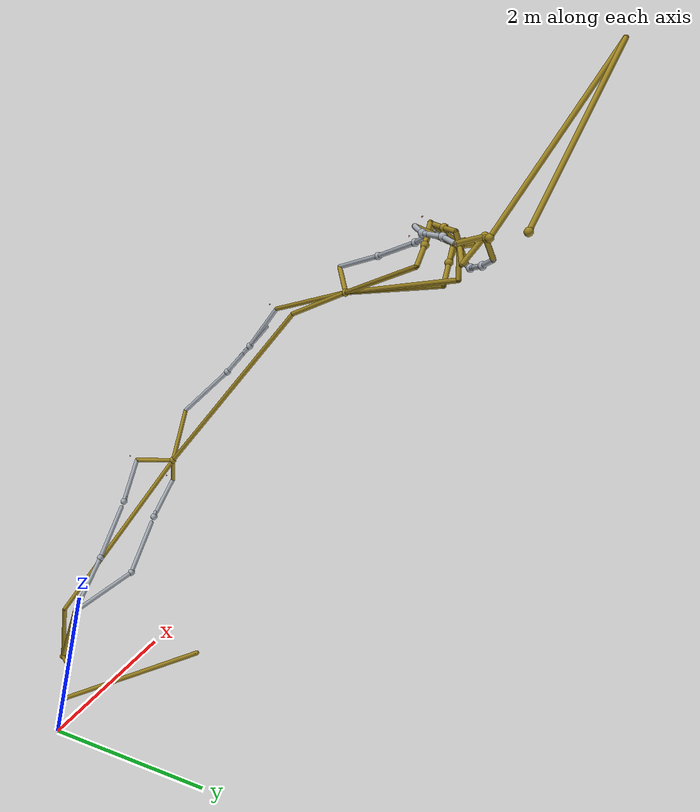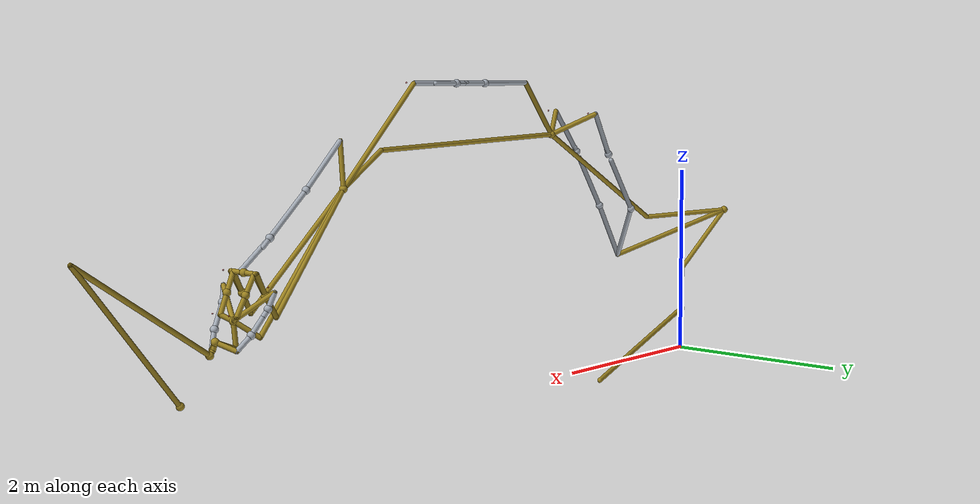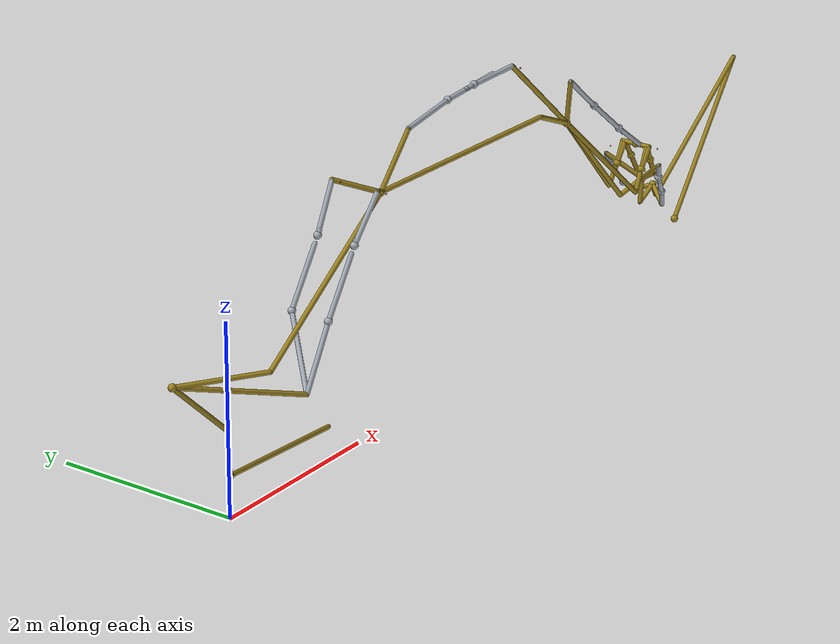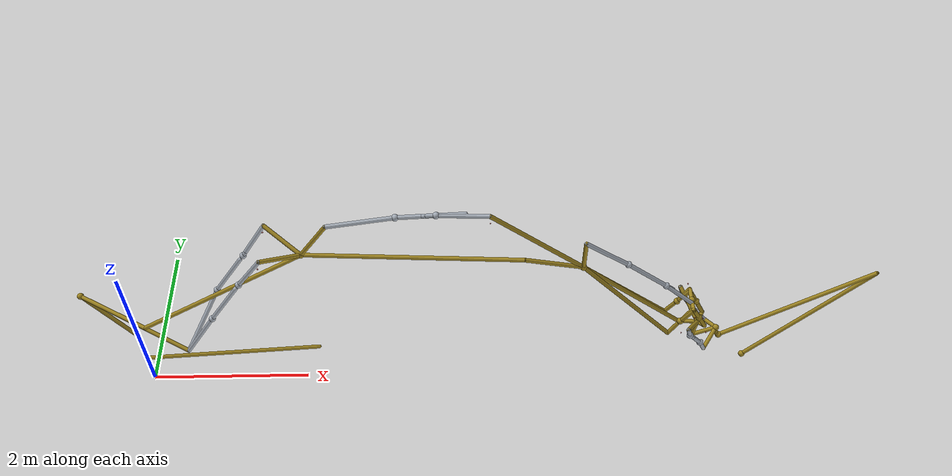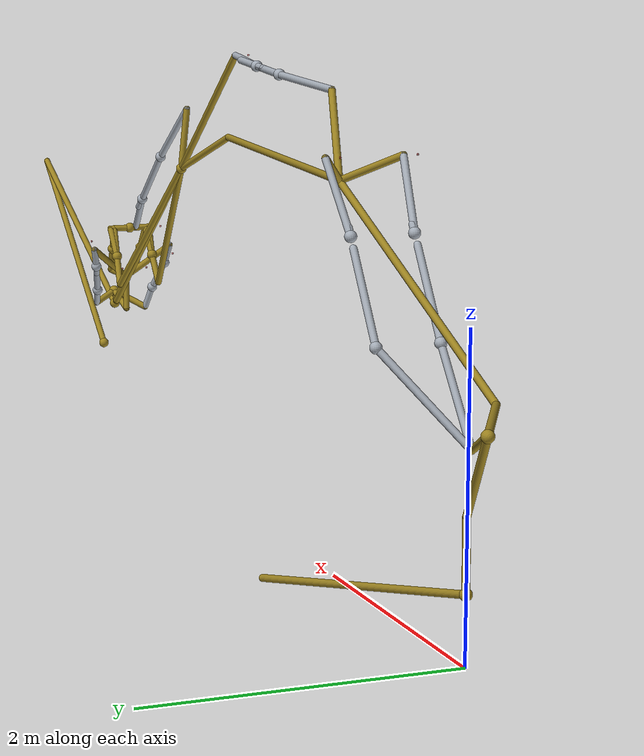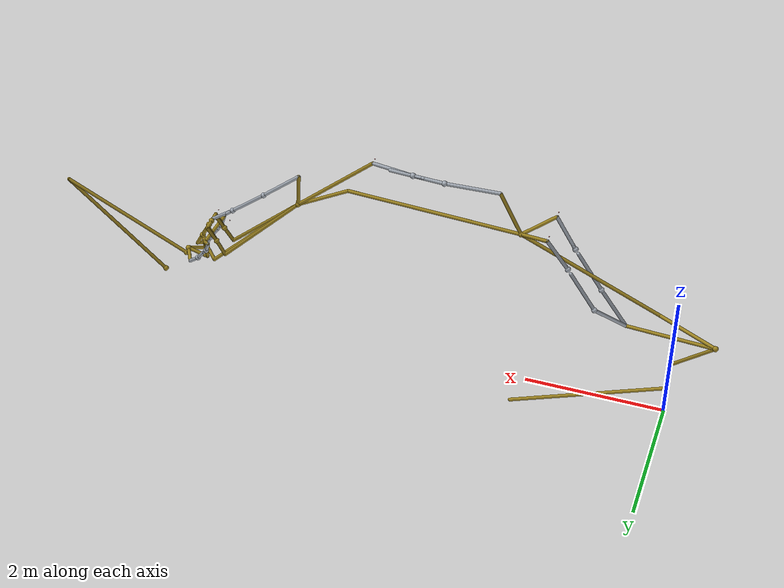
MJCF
<?xml version='1.0' encoding='utf-8'?>
<mujoco model="komatsu_excavator_source_snapshot_kinematics_v04">
  <compiler angle="radian" inertiafromgeom="false" fusestatic="false" balanceinertia="false" autolimits="false" />
  <option gravity="0 0 0" jacobian="dense">
    <flag contact="disable" />
  </option>
  <worldbody>
    <light pos="0 0 12" dir="0 0 -1" />
    <body name="body_53" pos="2.1126661182113513 0.45390271998685244 0" quat="0.70710678118654646 1.0453014276914226e-16 4.3297802811774738e-17 0.70710678118654879">
      <inertial mass="3532.1870348942721" pos="-0.45307654604025593 2.1068676260088073 0.44012497089198827" quat="0.70721396888326726 0.00044587027331154127 -0.00012322189401978392 0.70699942590672682" diaginertia="9926.7506261726885 10161.270821459639 18558.382359647319" />
      <geom name="visual_com_body_53" type="sphere" size="0.04" pos="-0.45307654604025593 2.1068676260088073 0.44012497089198827" rgba="0.62 0.52 0.13 1" contype="0" conaffinity="0" mass="0" />
      <geom name="visual_link_body_53_0" type="capsule" size="0.025" fromto="-0.45307654604025593 2.1068676260088073 0.44012497089198827 0 0 0" rgba="0.62 0.52 0.13 1" contype="0" conaffinity="0" mass="0" />
      <geom name="visual_link_body_53_1" type="capsule" size="0.025" fromto="-0.45307654604025593 2.1068676260088073 0.44012497089198827 -0.44707793770542764 2.1126656062104994 0.90213034042955353" rgba="0.62 0.52 0.13 1" contype="0" conaffinity="0" mass="0" />
      <body name="body_57" pos="-4.2806664522639775 3.1040482036329036 -0.067471228698529284" quat="0.7071067811865468 0.70710678118654824 3.9252311467094404e-17 1.5700924586837754e-16">
        <inertial mass="5230.0013622450278" pos="3.9941681672049389 1.5820059403962965 0.40855969935899628" quat="0.47153941014612721 0.31333908275081923 0.60413907723881044 -0.56078978169449234" diaginertia="27299.516633683128 51346.6841441383 63138.682317155319" />
        <joint name="q23" type="hinge" pos="3.8335885145585493 0.9696015691280836 0.99138259742240309" axis="2.2204460492503131e-16 1.0000000000000002 -1.9428902930940239e-15" ref="-1.5707963267948966" limited="false" damping="0" frictionloss="0" armature="0" stiffness="0" />
        <geom name="visual_com_body_57" type="sphere" size="0.04" pos="3.9941681672049389 1.5820059403962965 0.40855969935899628" rgba="0.62 0.52 0.13 1" contype="0" conaffinity="0" mass="0" />
        <geom name="visual_link_body_57_0" type="capsule" size="0.025" fromto="3.9941681672049389 1.5820059403962965 0.40855969935899628 3.8335885145585493 0.9696015691280836 0.99138259742240309" rgba="0.62 0.52 0.13 1" contype="0" conaffinity="0" mass="0" />
        <geom name="visual_link_body_57_1" type="capsule" size="0.025" fromto="3.9941681672049389 1.5820059403962965 0.40855969935899628 3.4650387751977032 1.1674481523732407 1.7069832520164276" rgba="0.62 0.52 0.13 1" contype="0" conaffinity="0" mass="0" />
        <geom name="visual_link_body_57_2" type="capsule" size="0.025" fromto="3.9941681672049389 1.5820059403962965 0.40855969935899628 3.5319065573122215 1.5474481523732408 1.2532832520164274" rgba="0.62 0.52 0.13 1" contype="0" conaffinity="0" mass="0" />
        <body name="body_1" pos="3.5000387751977033 1.1674481523732465 1.7069832520164117" quat="0.62244261219626351 -0.33550736880475818 0.6224426121962634 -0.33550736880475784">
          <inertial mass="60.951930879915047" pos="-0.70643958489259062 0.0010809256138337667 0" quat="0.99999999900897407 0 0 -4.4520242296722461e-05" diaginertia="0.02650833869847341 2.241912248708462 2.2422344619825845" />
          <joint name="q24" type="hinge" pos="-3.9612757518625585e-15 -1.6605383734713543e-14 -0.034999999999999955" axis="1.8102932767720225e-16 -1.4004883793903101e-16 1" ref="-2.55954063114521" limited="false" damping="0" frictionloss="0" armature="0" stiffness="0" />
          <geom name="visual_com_body_1" type="sphere" size="0.04" pos="-0.70643958489259062 0.0010809256138337667 0" rgba="0.65 0.68 0.72 1" contype="0" conaffinity="0" mass="0" />
          <geom name="visual_link_body_1_0" type="capsule" size="0.025" fromto="-0.70643958489259062 0.0010809256138337667 0 -1.3700000000000001 0.0010990275442380182 0" rgba="0.65 0.68 0.72 1" contype="0" conaffinity="0" mass="0" />
          <geom name="visual_link_body_1_1" type="capsule" size="0.025" fromto="-0.70643958489259062 0.0010809256138337667 0 -3.9612757518625585e-15 -1.6605383734713543e-14 -0.034999999999999955" rgba="0.65 0.68 0.72 1" contype="0" conaffinity="0" mass="0" />
          <body name="body_3" pos="-1.994474013728823 -2.2323722731476536e-15 -2.4763719293513217e-15" quat="2.1262266586035084e-31 -1.2490009027033033e-16 1 -3.9690473130349338e-15">
            <inertial mass="30.100532285979984" pos="-0.54216607696162955 0.0010246677329458756 5.3498727893530741e-10" quat="0.99999998874482032 -4.9787159573043724e-06 8.5395125473187027e-10 -0.00014995189785448054" diaginertia="0.0040027738513367427 0.71982756865482667 0.72000353932681416" />
            <joint name="p3" type="slide" pos="-0.4802298796567292 0.0010990275442401014 -2.5011104298755525e-15" axis="-1.0000000000000002 -1.1102230246251565e-16 1.1102230246251565e-16" ref="-0.14424413407209369" limited="false" damping="0" frictionloss="0" armature="0" stiffness="0" />
            <geom name="visual_com_body_3" type="sphere" size="0.04" pos="-0.54216607696162955 0.0010246677329458756 5.3498727893530741e-10" rgba="0.65 0.68 0.72 1" contype="0" conaffinity="0" mass="0" />
            <geom name="visual_link_body_3_0" type="capsule" size="0.025" fromto="-0.54216607696162955 0.0010246677329458756 5.3498727893530741e-10 -0.4802298796567292 0.0010990275442401014 -2.5011104298755525e-15" rgba="0.65 0.68 0.72 1" contype="0" conaffinity="0" mass="0" />
            <geom name="visual_link_body_3_1" type="capsule" size="0.025" fromto="-0.54216607696162955 0.0010246677329458756 5.3498727893530741e-10 -2.3590018827235327e-15 -2.9913849175500217e-15 0.050000000000022742" rgba="0.65 0.68 0.72 1" contype="0" conaffinity="0" mass="0" />
            <site name="frame_p3_follower" pos="-0.4802298796567292 0.0010990275442401014 -2.5011104298755525e-15" quat="0.499999999999998 -0.50000000000000211 -0.499999999999998 0.500000000000002" size="0.012" rgba="0.2 0.5 0.9 0.5" />
            <site name="frame_q5_follower" pos="-2.3590018827235327e-15 -2.9913849175500217e-15 0.050000000000022742" quat="1 1.7555192544547677e-17 -3.5920380213291133e-15 -6.3058919091768639e-32" size="0.012" rgba="0.2 0.5 0.9 0.5" />
            <site name="loop_q5_follower_0" pos="-2.3590018827235327e-15 -2.9913849175500217e-15 0.050000000000022742" size="0.008" rgba="0.9 0.2 0.2 0.5" />
            <site name="loop_q5_follower_1" pos="-3.0774094869893555e-15 -2.9948959560589311e-15 0.15000000000002275" size="0.008" rgba="0.9 0.2 0.2 0.5" />
            <site name="cylinder_pin_p3_follower" pos="-2.3590018827235327e-15 -2.9913849175500217e-15 0.050000000000022742" size="0.018" rgba="0.2 0.8 0.4 1" />
          </body>
          <site name="frame_p3_base" pos="-1.3700000000000001 0.0010990275442380182 0" quat="0.49999999999999994 0.50000000000000011 0.50000000000000011 0.50000000000000011" size="0.012" rgba="0.2 0.5 0.9 0.5" />
          <site name="frame_q24_follower" pos="-3.9612757518625585e-15 -1.6605383734713543e-14 -0.034999999999999955" quat="1 7.0024418969515506e-17 9.0514663838601124e-17 6.3382367435190597e-33" size="0.012" rgba="0.2 0.5 0.9 0.5" />
          <site name="cylinder_pin_p3_base" pos="-3.9612757518625585e-15 -1.6605383734713543e-14 -0.034999999999999955" size="0.018" rgba="0.2 0.8 0.4 1" />
        </body>
        <body name="body_2" pos="3.9300387751977031 1.1674481523732472 1.7069832520164099" quat="0.3355073688047584 0.62244261219626362 -0.33550736880475823 -0.62244261219626318">
          <inertial mass="60.951930879915047" pos="-0.70643958489259062 0.0010809256138337667 0" quat="0.99999999900897407 0 0 -4.4520242296722461e-05" diaginertia="0.02650833869847341 2.241912248708462 2.2422344619825845" />
          <joint name="q25" type="hinge" pos="-4.5190517994342373e-15 1.8303580873180181e-14 0.46499999999999975" axis="3.4338204938558158e-16 -1.2246467991473532e-16 -1" ref="-2.5595406311452109" limited="false" damping="0" frictionloss="0" armature="0" stiffness="0" />
          <geom name="visual_com_body_2" type="sphere" size="0.04" pos="-0.70643958489259062 0.0010809256138337667 0" rgba="0.65 0.68 0.72 1" contype="0" conaffinity="0" mass="0" />
          <geom name="visual_link_body_2_0" type="capsule" size="0.025" fromto="-0.70643958489259062 0.0010809256138337667 0 -1.3700000000000001 0.0010990275442379627 0" rgba="0.65 0.68 0.72 1" contype="0" conaffinity="0" mass="0" />
          <geom name="visual_link_body_2_1" type="capsule" size="0.025" fromto="-0.70643958489259062 0.0010809256138337667 0 -4.5190517994342373e-15 1.8303580873180181e-14 0.46499999999999975" rgba="0.65 0.68 0.72 1" contype="0" conaffinity="0" mass="0" />
          <body name="body_4" pos="-1.9944740137288233 -1.2932363513407097e-15 2.4121620926781593e-15" quat="2.1262266586035084e-31 -1.2490009027033033e-16 1 -3.9690473130349338e-15">
            <inertial mass="30.100532285979984" pos="-0.54216607696162955 0.0010246677329458756 5.3498727893530741e-10" quat="0.99999998874482032 -4.9787159573043724e-06 8.5395125473187027e-10 -0.00014995189785448054" diaginertia="0.0040027738513367427 0.71982756865482667 0.72000353932681416" />
            <joint name="p4" type="slide" pos="-0.48022987965672964 0.0010990275442391067 2.3874235921539368e-15" axis="-1.0000000000000002 -1.1102230246251565e-16 1.1102230246251565e-16" ref="-0.1442441340720936" limited="false" damping="0" frictionloss="0" armature="0" stiffness="0" />
            <geom name="visual_com_body_4" type="sphere" size="0.04" pos="-0.54216607696162955 0.0010246677329458756 5.3498727893530741e-10" rgba="0.65 0.68 0.72 1" contype="0" conaffinity="0" mass="0" />
            <geom name="visual_link_body_4_0" type="capsule" size="0.025" fromto="-0.54216607696162955 0.0010246677329458756 5.3498727893530741e-10 -0.48022987965672964 0.0010990275442391067 2.3874235921539368e-15" rgba="0.65 0.68 0.72 1" contype="0" conaffinity="0" mass="0" />
            <geom name="visual_link_body_4_1" type="capsule" size="0.025" fromto="-0.54216607696162955 0.0010246677329458756 5.3498727893530741e-10 1.808331262509455e-15 7.0130568019521888e-15 0.049999999999977493" rgba="0.65 0.68 0.72 1" contype="0" conaffinity="0" mass="0" />
            <site name="frame_p4_follower" pos="-0.48022987965672964 0.0010990275442391067 2.3874235921539368e-15" quat="0.499999999999998 -0.50000000000000211 -0.499999999999998 0.500000000000002" size="0.012" rgba="0.2 0.5 0.9 0.5" />
            <site name="frame_q6_follower" pos="1.808331262509455e-15 7.0130568019521888e-15 0.049999999999977493" quat="6.123233995736766e-17 1 -4.0007136821232808e-31 -3.5007303968825474e-15" size="0.012" rgba="0.2 0.5 0.9 0.5" />
            <site name="loop_q6_follower_0" pos="1.808331262509455e-15 7.0130568019521888e-15 0.049999999999977493" size="0.008" rgba="0.9 0.2 0.2 0.5" />
            <site name="loop_q6_follower_1" pos="1.1081851831329454e-15 7.0008103339607154e-15 -0.050000000000022513" size="0.008" rgba="0.9 0.2 0.2 0.5" />
            <site name="cylinder_pin_p4_follower" pos="1.808331262509455e-15 7.0130568019521888e-15 0.049999999999977493" size="0.018" rgba="0.2 0.8 0.4 1" />
          </body>
          <site name="frame_p4_base" pos="-1.3700000000000001 0.0010990275442379627 0" quat="0.49999999999999994 0.50000000000000011 0.50000000000000011 0.50000000000000011" size="0.012" rgba="0.2 0.5 0.9 0.5" />
          <site name="frame_q25_follower" pos="-4.5190517994342373e-15 1.8303580873180181e-14 0.46499999999999975" quat="6.123233995736766e-17 1 7.8818020661962999e-33 1.7169102469279079e-16" size="0.012" rgba="0.2 0.5 0.9 0.5" />
          <site name="cylinder_pin_p4_base" pos="-4.5190517994342373e-15 1.8303580873180181e-14 0.46499999999999975" size="0.018" rgba="0.2 0.8 0.4 1" />
        </body>
        <body name="body_54" pos="3.7150387751976872 1.5474481523732388 1.2532832520164097" quat="0.70183611446619054 -0.086174639140528045 -0.70183611446618965 0.086174639140535692">
          <inertial mass="1900.3523502528869" pos="2.1692225026399941 0.57825146021944129 7.6769544495436869e-08" quat="0.99947639414822442 -2.1957646338549157e-07 -6.3113659866020196e-08 -0.032356414208175935" diaginertia="483.17409454553314 7370.8186713638815 7761.0705397716383" />
          <joint name="q7" type="hinge" pos="1.7809266621026982e-14 -3.1263880373444406e-16 0.18313221788546563" axis="-1.4279165557080614e-16 1.081942037470899e-14 1" ref="-1.3264502315156905" limited="false" damping="0" frictionloss="0" armature="0" stiffness="0" />
          <geom name="visual_com_body_54" type="sphere" size="0.04" pos="2.1692225026399941 0.57825146021944129 7.6769544495436869e-08" rgba="0.62 0.52 0.13 1" contype="0" conaffinity="0" mass="0" />
          <geom name="visual_link_body_54_0" type="capsule" size="0.025" fromto="2.1692225026399941 0.57825146021944129 7.6769544495436869e-08 4.5999999999999988 2.2204460492503131e-16 0.13749999999999998" rgba="0.62 0.52 0.13 1" contype="0" conaffinity="0" mass="0" />
          <geom name="visual_link_body_54_1" type="capsule" size="0.025" fromto="2.1692225026399941 0.57825146021944129 7.6769544495436869e-08 1.8152200442459703 0.87284227924187019 0.26500000000000001" rgba="0.62 0.52 0.13 1" contype="0" conaffinity="0" mass="0" />
          <geom name="visual_link_body_54_2" type="capsule" size="0.025" fromto="2.1692225026399941 0.57825146021944129 7.6769544495436869e-08 1.8152200442459703 0.87284227924186975 -0.26500000000000001" rgba="0.62 0.52 0.13 1" contype="0" conaffinity="0" mass="0" />
          <geom name="visual_link_body_54_3" type="capsule" size="0.025" fromto="2.1692225026399941 0.57825146021944129 7.6769544495436869e-08 1.7809266621026982e-14 -3.1263880373444406e-16 0.18313221788546563" rgba="0.62 0.52 0.13 1" contype="0" conaffinity="0" mass="0" />
          <geom name="visual_link_body_54_4" type="capsule" size="0.025" fromto="2.1692225026399941 0.57825146021944129 7.6769544495436869e-08 2.6276426884144719 1.0376909877488327 0.079999999999999988" rgba="0.62 0.52 0.13 1" contype="0" conaffinity="0" mass="0" />
          <body name="body_44" pos="2.6276426884144897 1.0376909877488099 1.3877787807814457e-17" quat="7.8887356998007642e-17 0.0926974272160936 0.99569432407115643 1.0902044306085846e-16">
            <inertial mass="133.71247457463269" pos="-0.75400912577613988 0.0010648180152123153 7.8806346210309469e-10" quat="0.70710775245998592 -0.70710580660134204 4.8381411660147644e-05 -4.8382765533897523e-05" diaginertia="0.2490177818862413 26.331864227086623 26.339010712986578" />
            <joint name="q8" type="hinge" pos="2.163158541179655e-14 1.9241497284383514e-14 -0.079999999999999974" axis="1.1427699398109385e-16 -3.5208743051847803e-16 1" ref="-2.9559312566554605" limited="false" damping="0" frictionloss="0" armature="0" stiffness="0" />
            <geom name="visual_com_body_44" type="sphere" size="0.04" pos="-0.75400912577613988 0.0010648180152123153 7.8806346210309469e-10" rgba="0.65 0.68 0.72 1" contype="0" conaffinity="0" mass="0" />
            <geom name="visual_link_body_44_0" type="capsule" size="0.025" fromto="-0.75400912577613988 0.0010648180152123153 7.8806346210309469e-10 -1.5150000000000006 0.0010990275442379627 0" rgba="0.65 0.68 0.72 1" contype="0" conaffinity="0" mass="0" />
            <geom name="visual_link_body_44_1" type="capsule" size="0.025" fromto="-0.75400912577613988 0.0010648180152123153 7.8806346210309469e-10 2.163158541179655e-14 1.9241497284383514e-14 -0.079999999999999974" rgba="0.65 0.68 0.72 1" contype="0" conaffinity="0" mass="0" />
            <body name="body_45" pos="-1.7780679403796533 8.9338259012805565e-17 2.1254624522809463e-16" quat="8.3266726846886765e-17 -2.7755575615628909e-16 -1 -1.387778780781444e-17">
              <inertial mass="42.515992478803739" pos="-0.58186178905396513 0.0010269114084375485 4.8036804575692128e-10" quat="0.9999999907092525 -6.617461786380266e-06 1.0205340472285798e-09 -0.00013615323801515337" diaginertia="0.033460781605048777 6.8566327559976674 6.857743629288338" />
              <joint name="p5" type="slide" pos="-0.74275688247367322 0.0010990275442383393 1.4210854715202004e-16" axis="-1 6.6613381477509392e-16 -5.5511151231257827e-17" ref="0.4796889420940203" limited="false" damping="0" frictionloss="0" armature="0" stiffness="0" />
              <geom name="visual_com_body_45" type="sphere" size="0.04" pos="-0.58186178905396513 0.0010269114084375485 4.8036804575692128e-10" rgba="0.65 0.68 0.72 1" contype="0" conaffinity="0" mass="0" />
              <geom name="visual_link_body_45_0" type="capsule" size="0.025" fromto="-0.58186178905396513 0.0010269114084375485 4.8036804575692128e-10 -0.74275688247367322 0.0010990275442383393 1.4210854715202004e-16" rgba="0.65 0.68 0.72 1" contype="0" conaffinity="0" mass="0" />
              <geom name="visual_link_body_45_1" type="capsule" size="0.025" fromto="-0.58186178905396513 0.0010269114084375485 4.8036804575692128e-10 2.940603316403667e-13 -4.7392489932462921e-13 0.051999999999999165" rgba="0.65 0.68 0.72 1" contype="0" conaffinity="0" mass="0" />
              <site name="frame_p5_follower" pos="-0.74275688247367322 0.0010990275442383393 1.4210854715202004e-16" quat="0.50000000000000011 -0.50000000000000022 -0.49999999999999989 0.49999999999999989" size="0.012" rgba="0.2 0.5 0.9 0.5" />
              <site name="frame_q9_follower" pos="2.940603316403667e-13 -4.7392489932462921e-13 0.051999999999999165" quat="1 -2.2612797822699558e-16 4.5496727098427691e-17 -1.0288082914712817e-32" size="0.012" rgba="0.2 0.5 0.9 0.5" />
              <site name="loop_q9_follower_0" pos="2.940603316403667e-13 -4.7392489932462921e-13 0.051999999999999165" size="0.008" rgba="0.9 0.2 0.2 0.5" />
              <site name="loop_q9_follower_1" pos="2.9406943098578638e-13 -4.7387967372898379e-13 0.15199999999999916" size="0.008" rgba="0.9 0.2 0.2 0.5" />
              <site name="cylinder_pin_p5_follower" pos="2.940603316403667e-13 -4.7392489932462921e-13 0.051999999999999165" size="0.018" rgba="0.2 0.8 0.4 1" />
            </body>
            <site name="frame_p5_base" pos="-1.5150000000000006 0.0010990275442379627 0" quat="0.49999999999999994 0.50000000000000011 0.50000000000000011 0.50000000000000011" size="0.012" rgba="0.2 0.5 0.9 0.5" />
            <site name="frame_q8_follower" pos="2.163158541179655e-14 1.9241497284383514e-14 -0.079999999999999974" quat="1 1.7604371525923901e-16 5.7138496990546924e-17 1.0058873294544725e-32" size="0.012" rgba="0.2 0.5 0.9 0.5" />
            <site name="cylinder_pin_p5_base" pos="2.163158541179655e-14 1.9241497284383514e-14 -0.079999999999999974" size="0.018" rgba="0.2 0.8 0.4 1" />
          </body>
          <body name="body_60" pos="4.6000000000004473 -3.1459914271094241e-13 -6.6613381477509392e-16" quat="0.63554336502823694 0.63554336502823672 -0.30997521057108002 -0.30997521057108013">
            <inertial mass="1050.8289000323198" pos="0.73117001896287481 0 -0.18553198908280619" quat="0.044096197805118087 -0.04409619780511808 0.70573049058343218 0.7057304905834324" diaginertia="61.582764611835934 1801.5852056927888 1835.077090678147" />
            <joint name="q4" type="hinge" pos="-5.2445678267467939e-13 0.13750000000000068 1.5994277547702801e-13" axis="1.1102230246251565e-16 -0.99999999999999989 -1.1102230246251565e-16" ref="-3.8048177693476384" limited="false" damping="0" frictionloss="0" armature="0" stiffness="0" />
            <geom name="visual_com_body_60" type="sphere" size="0.04" pos="0.73117001896287481 0 -0.18553198908280619" rgba="0.62 0.52 0.13 1" contype="0" conaffinity="0" mass="0" />
            <geom name="visual_link_body_60_0" type="capsule" size="0.025" fromto="0.73117001896287481 0 -0.18553198908280619 2.5000000000000018 -0.14000000000000007 0" rgba="0.62 0.52 0.13 1" contype="0" conaffinity="0" mass="0" />
            <geom name="visual_link_body_60_1" type="capsule" size="0.025" fromto="0.73117001896287481 0 -0.18553198908280619 0.44408080485725893 0.044340000000000018 -0.54077884848512536" rgba="0.62 0.52 0.13 1" contype="0" conaffinity="0" mass="0" />
            <geom name="visual_link_body_60_2" type="capsule" size="0.025" fromto="0.73117001896287481 0 -0.18553198908280619 2.2504342363294612 0.16500000000000001 -0.014728530257288597" rgba="0.62 0.52 0.13 1" contype="0" conaffinity="0" mass="0" />
            <geom name="visual_link_body_60_3" type="capsule" size="0.025" fromto="0.73117001896287481 0 -0.18553198908280619 2.2504342363294612 -0.16500000000000004 -0.014728530257288597" rgba="0.62 0.52 0.13 1" contype="0" conaffinity="0" mass="0" />
            <geom name="visual_link_body_60_4" type="capsule" size="0.025" fromto="0.73117001896287481 0 -0.18553198908280619 -5.2445678267467939e-13 0.13750000000000068 1.5994277547702801e-13" rgba="0.62 0.52 0.13 1" contype="0" conaffinity="0" mass="0" />
            <geom name="visual_link_body_60_5" type="capsule" size="0.025" fromto="0.73117001896287481 0 -0.18553198908280619 -0.69749596646377032 0.051999999999999991 -0.25960916514653309" rgba="0.62 0.52 0.13 1" contype="0" conaffinity="0" mass="0" />
            <body name="body_5" pos="0.44408080485697149 -2.0816681711721685e-17 -0.54077884848506463" quat="0.0072919325201678854 0.0072919325201681959 0.70706918170722277 -0.70706918170722244">
              <inertial mass="40.957885921643921" pos="-0.66743919532559559 0.00107535960943833 -2.0963088740655773e-10" quat="0.99999999822465135 -4.7799810023524181e-07 7.6461927581102378e-10 -5.9585811156317218e-05" diaginertia="0.19917478471388234 15.553333185335454 15.55527416808973" />
              <joint name="q10" type="hinge" pos="-2.8608582169908912e-13 6.6641803186939793e-14 -0.044340000000000046" axis="-5.5097040039254427e-16 -6.7678718909544881e-17 1" ref="1.5914213920983555" limited="false" damping="0" frictionloss="0" armature="0" stiffness="0" />
              <geom name="visual_com_body_5" type="sphere" size="0.04" pos="-0.66743919532559559 0.00107535960943833 -2.0963088740655773e-10" rgba="0.65 0.68 0.72 1" contype="0" conaffinity="0" mass="0" />
              <geom name="visual_link_body_5_0" type="capsule" size="0.025" fromto="-0.66743919532559559 0.00107535960943833 -2.0963088740655773e-10 -1.3050000000000002 0.0010990275442370745 0" rgba="0.65 0.68 0.72 1" contype="0" conaffinity="0" mass="0" />
              <geom name="visual_link_body_5_1" type="capsule" size="0.025" fromto="-0.66743919532559559 0.00107535960943833 -2.0963088740655773e-10 -2.8608582169908912e-13 6.6641803186939793e-14 -0.044340000000000046" rgba="0.65 0.68 0.72 1" contype="0" conaffinity="0" mass="0" />
              <body name="body_6" pos="-1.738001721036647 -1.40989650510015e-15 -6.5736006250326676e-17" quat="5.5511151231257839e-17 -1.6653345369377346e-16 -1 -5.5511151231257815e-17">
                <inertial mass="25.380614798072777" pos="-0.44380475649582318 0.001021336930564174 -6.4793980766272311e-08" quat="0.99999998246742727 -3.1650236975412821e-06 9.6239214019229012e-08 -0.00018723012233005441" diaginertia="0.027495329533117712 3.2986552937164144 3.2999081856521983" />
                <joint name="p2" type="slide" pos="-0.3247486779716125 0.0010990275442385809 -1.1368683772161603e-16" axis="-1 4.4408920985006262e-16 0" ref="-0.10825304306503437" limited="false" damping="0" frictionloss="0" armature="0" stiffness="0" />
                <geom name="visual_com_body_6" type="sphere" size="0.04" pos="-0.44380475649582318 0.001021336930564174 -6.4793980766272311e-08" rgba="0.65 0.68 0.72 1" contype="0" conaffinity="0" mass="0" />
                <geom name="visual_link_body_6_0" type="capsule" size="0.025" fromto="-0.44380475649582318 0.001021336930564174 -6.4793980766272311e-08 -0.3247486779716125 0.0010990275442385809 -1.1368683772161603e-16" rgba="0.65 0.68 0.72 1" contype="0" conaffinity="0" mass="0" />
                <geom name="visual_link_body_6_1" type="capsule" size="0.025" fromto="-0.44380475649582318 0.001021336930564174 -6.4793980766272311e-08 -2.2932766796657232e-13 1.836752971939859e-14 0.051999999999999984" rgba="0.65 0.68 0.72 1" contype="0" conaffinity="0" mass="0" />
                <body name="body_59" pos="-2.2939993553725396e-13 1.7473460403786913e-14 -2.7755575615639218e-17" quat="0.77657350584918294 -2.8721024679562409e-17 -3.6561075587340173e-18 0.63002665817654813">
                  <inertial mass="9.0288842720410383" pos="0 0 0" quat="0.70710678118654757 0 0.70710678118654746 -0" diaginertia="0.0050334752427875261 0.08091622290306015 0.08091622290306015" />
                  <joint name="q22" type="hinge" pos="8.8817841970012523e-16 1.1102230246251565e-16 0.052000000000000011" axis="-0 -0 -1" ref="-1.3631750780704177" limited="false" damping="0" frictionloss="0" armature="0" stiffness="0" />
                  <geom name="visual_com_body_59" type="sphere" size="0.04" pos="0 0 0" rgba="0.62 0.52 0.13 1" contype="0" conaffinity="0" mass="0" />
                  <geom name="visual_link_body_59_0" type="capsule" size="0.025" fromto="0 0 0 -3.2232289104414539e-13 -2.9143905067030572e-12 0.16500000000000103" rgba="0.62 0.52 0.13 1" contype="0" conaffinity="0" mass="0" />
                  <geom name="visual_link_body_59_1" type="capsule" size="0.025" fromto="0 0 0 -3.2250885251286206e-13 -2.9135094337107149e-12 -0.16499999999999915" rgba="0.62 0.52 0.13 1" contype="0" conaffinity="0" mass="0" />
                  <geom name="visual_link_body_59_2" type="capsule" size="0.025" fromto="0 0 0 8.8817841970012523e-16 1.1102230246251565e-16 0.052000000000000011" rgba="0.62 0.52 0.13 1" contype="0" conaffinity="0" mass="0" />
                  <site name="frame_q15_follower" pos="-3.2232289104414539e-13 -2.9143905067030572e-12 0.16500000000000103" quat="1 1.0232102034168834e-16 -2.9131097538445411e-18 -2.9807236238069801e-34" size="0.012" rgba="0.2 0.5 0.9 0.5" />
                  <site name="frame_q18_follower" pos="-3.2250885251286206e-13 -2.9135094337107149e-12 -0.16499999999999915" quat="1 -2.8086482888216172e-16 1.2549041137639666e-16 -3.5245842917583721e-32" size="0.012" rgba="0.2 0.5 0.9 0.5" />
                  <site name="frame_q22_base" pos="8.8817841970012523e-16 1.1102230246251565e-16 0.052000000000000011" quat="1 0 0 0" size="0.012" rgba="0.2 0.5 0.9 0.5" />
                  <site name="loop_q15_follower_0" pos="-3.2232289104414539e-13 -2.9143905067030572e-12 0.16500000000000103" size="0.008" rgba="0.9 0.2 0.2 0.5" />
                  <site name="loop_q15_follower_1" pos="-3.2232347366609616e-13 -2.9144109709071257e-12 0.26500000000000101" size="0.008" rgba="0.9 0.2 0.2 0.5" />
                  <site name="loop_q18_follower_0" pos="-3.2250885251286206e-13 -2.9135094337107149e-12 -0.16499999999999915" size="0.008" rgba="0.9 0.2 0.2 0.5" />
                  <site name="loop_q18_follower_1" pos="-3.2248375443058676e-13 -2.9134532607449386e-12 -0.064999999999999142" size="0.008" rgba="0.9 0.2 0.2 0.5" />
                </body>
                <site name="frame_p2_follower" pos="-0.3247486779716125 0.0010990275442385809 -1.1368683772161603e-16" quat="0.50000000000000011 -0.50000000000000011 -0.49999999999999989 0.49999999999999989" size="0.012" rgba="0.2 0.5 0.9 0.5" />
                <site name="frame_q22_follower" pos="-2.2932766796657232e-13 1.836752971939859e-14 0.051999999999999984" quat="1 -2.0000541599825477e-17 -2.0934247462918639e-17 4.186962872431452e-34" size="0.012" rgba="0.2 0.5 0.9 0.5" />
                <site name="cylinder_pin_p2_follower" pos="-2.2932766796657232e-13 1.836752971939859e-14 0.051999999999999984" size="0.018" rgba="0.2 0.8 0.4 1" />
              </body>
              <site name="frame_p2_base" pos="-1.3050000000000002 0.0010990275442370745 0" quat="0.49999999999999994 0.50000000000000011 0.50000000000000011 0.50000000000000011" size="0.012" rgba="0.2 0.5 0.9 0.5" />
              <site name="frame_q10_follower" pos="-2.8608582169908912e-13 6.6641803186939793e-14 -0.044340000000000046" quat="1 3.383935945477244e-17 -2.7548520019627214e-16 -9.3222427139116004e-33" size="0.012" rgba="0.2 0.5 0.9 0.5" />
              <site name="cylinder_pin_p2_base" pos="-2.8608582169908912e-13 6.6641803186939793e-14 -0.044340000000000046" size="0.018" rgba="0.2 0.8 0.4 1" />
            </body>
            <body name="body_61" pos="2.633585019020614 0.33963737029227076 0.006456566156616694" quat="2.4814041817589647e-16 0.58665935450404361 -4.1238205860972464e-16 0.80983381120628639">
              <inertial mass="104.22805452982625" pos="-0.21972090812718234 0.33477380234641207 -0.15673837543458147" quat="0.99633368219728846 -0.006982614735663837 0.07598359059278581 -0.038690189599870188" diaginertia="4.5421341339168597 5.0795767728248871 6.5409078485292991" />
              <joint name="q0" type="hinge" pos="0.035498336226444993 0.47963737029227099 -0.12894383536418583" axis="-2.2204460492503131e-16 -1 -8.8817841970012523e-16" ref="1.2538550938747008" limited="false" damping="0" frictionloss="0" armature="0" stiffness="0" />
              <geom name="visual_com_body_61" type="sphere" size="0.04" pos="-0.21972090812718234 0.33477380234641207 -0.15673837543458147" rgba="0.62 0.52 0.13 1" contype="0" conaffinity="0" mass="0" />
              <geom name="visual_link_body_61_0" type="capsule" size="0.025" fromto="-0.21972090812718234 0.33477380234641207 -0.15673837543458147 0.035498336226444993 0.47963737029227099 -0.12894383536418583" rgba="0.62 0.52 0.13 1" contype="0" conaffinity="0" mass="0" />
              <geom name="visual_link_body_61_1" type="capsule" size="0.025" fromto="-0.21972090812718234 0.33477380234641207 -0.15673837543458147 -0.049753014868739953 0.33963737029228325 0.04869248784312119" rgba="0.62 0.52 0.13 1" contype="0" conaffinity="0" mass="0" />
              <geom name="visual_link_body_61_2" type="capsule" size="0.025" fromto="-0.21972090812718234 0.33477380234641207 -0.15673837543458147 -0.30342205754230817 0.23463737029224341 -0.16579443491783827" rgba="0.62 0.52 0.13 1" contype="0" conaffinity="0" mass="0" />
              <geom name="visual_link_body_61_3" type="capsule" size="0.025" fromto="-0.21972090812718234 0.33477380234641207 -0.15673837543458147 -0.21193662431119442 0.014637370292039931 -0.49329780478496577" rgba="0.62 0.52 0.13 1" contype="0" conaffinity="0" mass="0" />
              <geom name="visual_link_body_61_4" type="capsule" size="0.025" fromto="-0.21972090812718234 0.33477380234641207 -0.15673837543458147 -0.30342205754230828 0.44463737029229855 -0.16579443491783333" rgba="0.62 0.52 0.13 1" contype="0" conaffinity="0" mass="0" />
              <geom name="visual_link_body_61_5" type="capsule" size="0.025" fromto="-0.21972090812718234 0.33477380234641207 -0.15673837543458147 -0.20194271604100233 0.6646373702924967 -0.49294880981793332" rgba="0.62 0.52 0.13 1" contype="0" conaffinity="0" mass="0" />
              <body name="body_58" pos="-0.0004996954141160484 -2.5218716004360431e-13 -1.744975152020295e-05" quat="1 -7.5930919593753501e-16 -3.2124280033024989e-13 2.4419404356429601e-14">
                <inertial mass="140.29614001342856" pos="-0.34331722877607013 0.35998725296241346 0.11623130162140567" quat="0.98938507358463568 0.00513940284601473 -0.013539624378447737 -0.14459405685574392" diaginertia="2.1113898204286468 3.5504649222080817 5.1714516080775468" />
                <joint name="q1" type="hinge" pos="-0.049253319454576033 0.33963737029253782 0.048709937594673548" axis="0.99939082701911774 -4.8960835385969403e-14 0.034899496701866428" ref="0" limited="false" damping="0" frictionloss="0" armature="0" stiffness="0" />
                <geom name="visual_com_body_58" type="sphere" size="0.04" pos="-0.34331722877607013 0.35998725296241346 0.11623130162140567" rgba="0.62 0.52 0.13 1" contype="0" conaffinity="0" mass="0" />
                <geom name="visual_link_body_58_0" type="capsule" size="0.025" fromto="-0.34331722877607013 0.35998725296241346 0.11623130162140567 -0.049253319454576033 0.33963737029253782 0.048709937594673548" rgba="0.62 0.52 0.13 1" contype="0" conaffinity="0" mass="0" />
                <geom name="visual_link_body_58_1" type="capsule" size="0.025" fromto="-0.34331722877607013 0.35998725296241346 0.11623130162140567 -0.13816738771396597 0.13963737029232703 0.13065679874841565" rgba="0.62 0.52 0.13 1" contype="0" conaffinity="0" mass="0" />
                <geom name="visual_link_body_58_2" type="capsule" size="0.025" fromto="-0.34331722877607013 0.35998725296241346 0.11623130162140567 -0.22211621718357044 0.53963737029226744 0.12772524102540495" rgba="0.62 0.52 0.13 1" contype="0" conaffinity="0" mass="0" />
                <geom name="visual_link_body_58_3" type="capsule" size="0.025" fromto="-0.34331722877607013 0.35998725296241346 0.11623130162140567 -0.30715962567395838 0.33963737029228019 0.18479203372851771" rgba="0.62 0.52 0.13 1" contype="0" conaffinity="0" mass="0" />
                <body name="body_46" pos="-0.18014180244807113 0.13963737029268641 0.12919101989022688" quat="0.44007297875731255 -0.5565780609180786 -0.45570890978299372 0.53748118573279646">
                  <inertial mass="30.749166698137497" pos="2.1021574400713994e-08 0.1955859950725623 3.3690153788325436e-13" quat="0.50000376398643442 0.49999632888661499 -0.49999623598833659 -0.50000367108332466" diaginertia="0.0097562679557728661 0.19110579221699489 0.19147047942805967" />
                  <joint name="q11" type="hinge" pos="2.9363178555286142e-13 3.2695979257368892e-12 -0.041999999999187826" axis="-7.9065498005101507e-14 -6.4049910528370505e-13 -1" ref="-0.19863394992755873" limited="false" damping="0" frictionloss="0" armature="0" stiffness="0" />
                  <geom name="visual_com_body_46" type="sphere" size="0.04" pos="2.1021574400713994e-08 0.1955859950725623 3.3690153788325436e-13" rgba="0.65 0.68 0.72 1" contype="0" conaffinity="0" mass="0" />
                  <geom name="visual_link_body_46_0" type="capsule" size="0.025" fromto="2.1021574400713994e-08 0.1955859950725623 3.3690153788325436e-13 0 0.39500000000000024 -8.8817841970012523e-16" rgba="0.65 0.68 0.72 1" contype="0" conaffinity="0" mass="0" />
                  <geom name="visual_link_body_46_1" type="capsule" size="0.025" fromto="2.1021574400713994e-08 0.1955859950725623 3.3690153788325436e-13 2.9363178555286142e-13 3.2695979257368892e-12 -0.041999999999187826" rgba="0.65 0.68 0.72 1" contype="0" conaffinity="0" mass="0" />
                  <body name="body_48" pos="0.56035232276315394 0.030499329628834226 0.17552336335742708" quat="0.55483901949097147 0.44211612602463968 -0.53580181294739104 0.45782465071416983">
                    <inertial mass="10.237596828547654" pos="-0.16357157716962112 0.63568340722660022 -0.34178964096683728" quat="0.69110987058085549 0.068564127439157962 -0.71643056114604631 -0.066282412977964375" diaginertia="0.001154283769031798 0.055889780519588456 0.056114693169053674" />
                    <joint name="p0" type="slide" pos="-0.16663982870015348 0.61936422803443747 -0.25745492019702704" axis="-0.034264716887534921 -0.18985984061482691 0.98121311145863199" ref="-2.3815421693502969e-13" limited="false" damping="0" frictionloss="0" armature="0" stiffness="0" />
                    <geom name="visual_com_body_48" type="sphere" size="0.04" pos="-0.16357157716962112 0.63568340722660022 -0.34178964096683728" rgba="0.65 0.68 0.72 1" contype="0" conaffinity="0" mass="0" />
                    <geom name="visual_link_body_48_0" type="capsule" size="0.025" fromto="-0.16357157716962112 0.63568340722660022 -0.34178964096683728 -0.16663982870015348 0.61936422803443747 -0.25745492019702704" rgba="0.65 0.68 0.72 1" contype="0" conaffinity="0" mass="0" />
                    <geom name="visual_link_body_48_1" type="capsule" size="0.025" fromto="-0.16357157716962112 0.63568340722660022 -0.34178964096683728 -0.10550150123396318 0.66463737029920888 -0.48958100837684493" rgba="0.65 0.68 0.72 1" contype="0" conaffinity="0" mass="0" />
                    <site name="frame_p0_follower" pos="-0.16663982870015348 0.61936422803443747 -0.25745492019702704" quat="0.99529080458858588 0.095350027849776489 -0.017372865616555433 0.0016643409270251999" size="0.012" rgba="0.2 0.5 0.9 0.5" />
                    <site name="frame_q2_follower" pos="-0.10550150123396318 0.66463737029920888 -0.48958100837684493" quat="0.49119764435955215 -0.50865005079683911 -0.508650050796839 0.49119764435955193" size="0.012" rgba="0.2 0.5 0.9 0.5" />
                    <site name="loop_q2_follower_0" pos="-0.10550150123396318 0.66463737029920888 -0.48958100837684493" size="0.008" rgba="0.9 0.2 0.2 0.5" />
                    <site name="loop_q2_follower_1" pos="-0.20544058393587275 0.66463737029920888 -0.49307095804709578" size="0.008" rgba="0.9 0.2 0.2 0.5" />
                    <site name="cylinder_pin_p0_follower" pos="-0.10550150123396318 0.66463737029920888 -0.48958100837684493" size="0.018" rgba="0.2 0.8 0.4 1" />
                  </body>
                  <site name="frame_p0_base" pos="0 0.39500000000000024 -8.8817841970012523e-16" quat="0.49999999999999994 0.50000000000000011 -0.50000000000000011 0.50000000000000011" size="0.012" rgba="0.2 0.5 0.9 0.5" />
                  <site name="frame_q11_follower" pos="2.9363178555286142e-13 3.2695979257368892e-12 -0.041999999999187826" quat="3.2024955264185253e-13 1 -1.2663020625831104e-26 -3.9532749002550754e-14" size="0.012" rgba="0.2 0.5 0.9 0.5" />
                  <site name="cylinder_pin_p0_base" pos="2.9363178555286142e-13 3.2695979257368892e-12 -0.041999999999187826" size="0.018" rgba="0.2 0.8 0.4 1" />
                </body>
                <body name="body_47" pos="-0.18014180244876843 0.53963737029226744 0.12919101988691037" quat="0.5374811857325954 -0.45570890978319017 -0.55657806091820705 0.44007297875719248">
                  <inertial mass="30.749166698137497" pos="2.1021574400713994e-08 0.1955859950725623 3.3690153788325436e-13" quat="0.50000376398643442 0.49999632888661499 -0.49999623598833659 -0.50000367108332466" diaginertia="0.0097562679557728661 0.19110579221699489 0.19147047942805967" />
                  <joint name="q12" type="hinge" pos="-2.1316282072803006e-17 7.105427357601002e-18 0.042000000000000003" axis="2.7599180131041915e-16 -5.3035942839521701e-16 1" ref="-0.19863394992740921" limited="false" damping="0" frictionloss="0" armature="0" stiffness="0" />
                  <geom name="visual_com_body_47" type="sphere" size="0.04" pos="2.1021574400713994e-08 0.1955859950725623 3.3690153788325436e-13" rgba="0.65 0.68 0.72 1" contype="0" conaffinity="0" mass="0" />
                  <geom name="visual_link_body_47_0" type="capsule" size="0.025" fromto="2.1021574400713994e-08 0.1955859950725623 3.3690153788325436e-13 0 0.39499999999999991 0" rgba="0.65 0.68 0.72 1" contype="0" conaffinity="0" mass="0" />
                  <geom name="visual_link_body_47_1" type="capsule" size="0.025" fromto="2.1021574400713994e-08 0.1955859950725623 3.3690153788325436e-13 -2.1316282072803006e-17 7.105427357601002e-18 0.042000000000000003" rgba="0.65 0.68 0.72 1" contype="0" conaffinity="0" mass="0" />
                  <body name="body_49" pos="0.56035232276315583 0.03049932962881452 0.17552336335742644" quat="0.55483901949097125 0.4421161260246399 -0.53580181294739104 0.45782465071416967">
                    <inertial mass="10.237596828547654" pos="-0.16357157716962112 0.63568340722660022 -0.34178964096683728" quat="0.69110987058085549 0.068564127439157962 -0.71643056114604631 -0.066282412977964375" diaginertia="0.001154283769031798 0.055889780519588456 0.056114693169053674" />
                    <joint name="p1" type="slide" pos="-0.166639828700168 0.6193642280343522 -0.25745492019657729" axis="-0.034264716887533977 -0.18985984061482655 0.98121311145863199" ref="2.3927524686488052e-13" limited="false" damping="0" frictionloss="0" armature="0" stiffness="0" />
                    <geom name="visual_com_body_49" type="sphere" size="0.04" pos="-0.16357157716962112 0.63568340722660022 -0.34178964096683728" rgba="0.65 0.68 0.72 1" contype="0" conaffinity="0" mass="0" />
                    <geom name="visual_link_body_49_0" type="capsule" size="0.025" fromto="-0.16357157716962112 0.63568340722660022 -0.34178964096683728 -0.166639828700168 0.6193642280343522 -0.25745492019657729" rgba="0.65 0.68 0.72 1" contype="0" conaffinity="0" mass="0" />
                    <geom name="visual_link_body_49_1" type="capsule" size="0.025" fromto="-0.16357157716962112 0.63568340722660022 -0.34178964096683728 -0.11549540950469762 0.664637370297673 -0.48993000334090564" rgba="0.65 0.68 0.72 1" contype="0" conaffinity="0" mass="0" />
                    <site name="frame_p1_follower" pos="-0.166639828700168 0.6193642280343522 -0.25745492019657729" quat="0.99529080458858588 0.095350027849776309 -0.017372865616554965 0.0016643409270252361" size="0.012" rgba="0.2 0.5 0.9 0.5" />
                    <site name="frame_q3_follower" pos="-0.11549540950469762 0.664637370297673 -0.48993000334090564" quat="0.50865005079705172 0.49119764435947944 0.49119764435933178 0.5086500507969095" size="0.012" rgba="0.2 0.5 0.9 0.5" />
                    <site name="loop_q3_follower_0" pos="-0.11549540950469762 0.664637370297673 -0.48993000334090564" size="0.008" rgba="0.9 0.2 0.2 0.5" />
                    <site name="loop_q3_follower_1" pos="-0.01555632680279008 0.66463737029764403 -0.48644005367059728" size="0.008" rgba="0.9 0.2 0.2 0.5" />
                    <site name="cylinder_pin_p1_follower" pos="-0.11549540950469762 0.664637370297673 -0.48993000334090564" size="0.018" rgba="0.2 0.8 0.4 1" />
                  </body>
                  <site name="frame_p1_base" pos="0 0.39499999999999991 0" quat="0.49999999999999994 0.50000000000000011 -0.50000000000000011 0.50000000000000011" size="0.012" rgba="0.2 0.5 0.9 0.5" />
                  <site name="frame_q12_follower" pos="-2.1316282072803006e-17 7.105427357601002e-18 0.042000000000000003" quat="1 2.6517971419760851e-16 1.3799590065520957e-16 3.6593713496190046e-32" size="0.012" rgba="0.2 0.5 0.9 0.5" />
                  <site name="cylinder_pin_p1_base" pos="-2.1316282072803006e-17 7.105427357601002e-18 0.042000000000000003" size="0.018" rgba="0.2 0.8 0.4 1" />
                </body>
                <body name="body_55" pos="0.042854338814075521 0.0080107450148048098 -0.26124482181406034" quat="1 3.2899614453230435e-18 1.0405170615848126e-17 8.4497832689985226e-34">
                  <inertial mass="48.301864346291183" pos="-0.36300229439738707 0.33162662527735404 0.50385264229332916" quat="0.999948917345716 2.0911614903034748e-06 -0.01009726787172993 0.00045593451728758339" diaginertia="0.66072314918764741 1.0698799049537639 1.4798098762129881" />
                  <joint name="q21" type="hinge" pos="-0.35001396448803396 0.33162662527747538 0.4460368555425781" axis="-0.034899496702507457 -1.3914085737861523e-16 0.99939082701909543" ref="0" limited="false" damping="0" frictionloss="0" armature="0" stiffness="0" />
                  <geom name="visual_com_body_55" type="sphere" size="0.04" pos="-0.36300229439738707 0.33162662527735404 0.50385264229332916" rgba="0.62 0.52 0.13 1" contype="0" conaffinity="0" mass="0" />
                  <geom name="visual_link_body_55_0" type="capsule" size="0.025" fromto="-0.36300229439738707 0.33162662527735404 0.50385264229332916 -2.3473505457080757 0.4397998193679854 0.59342675960514901" rgba="0.62 0.52 0.13 1" contype="0" conaffinity="0" mass="0" />
                  <geom name="visual_link_body_55_1" type="capsule" size="0.025" fromto="-0.36300229439738707 0.33162662527735404 0.50385264229332916 -0.35001396448803396 0.33162662527747538 0.4460368555425781" rgba="0.62 0.52 0.13 1" contype="0" conaffinity="0" mass="0" />
                  <body name="body_56" pos="-2.3473505457080757 0.4397998193679854 0.59342675960514901" quat="0.70468251513288993 0.058502588540886413 0.058502588540886483 0.70468251513289004">
                    <inertial mass="400.0964996070096" pos="-0.11782204299559358 -1.807825290669232 0.76256974866745963" quat="0.65858625211847965 0.057839141544353219 0.23426758203323803 -0.71276748118460553" diaginertia="162.6991348111363 240.9822163090781 255.17066667017653" />
                    <geom name="visual_com_body_56" type="sphere" size="0.04" pos="-0.11782204299559358 -1.807825290669232 0.76256974866745963" rgba="0.62 0.52 0.13 1" contype="0" conaffinity="0" mass="0" />
                    <geom name="visual_link_body_56_0" type="capsule" size="0.025" fromto="-0.11782204299559358 -1.807825290669232 0.76256974866745963 0 0 0" rgba="0.62 0.52 0.13 1" contype="0" conaffinity="0" mass="0" />
                    <site name="frame_fixed_bucket_mount_follower" pos="0 0 0" quat="1 0 0 0" size="0.012" rgba="0.2 0.5 0.9 0.5" />
                  </body>
                  <site name="frame_fixed_bucket_mount_base" pos="-2.3473505457080757 0.4397998193679854 0.59342675960514901" quat="0.70468251513288993 0.058502588540886413 0.058502588540886483 0.70468251513289004" size="0.012" rgba="0.2 0.5 0.9 0.5" />
                  <site name="frame_q21_follower" pos="-0.35001396448803396 0.33162662527747538 0.4460368555425781" quat="0.99984769515639116 6.9602232575541941e-17 -0.017452406437286759 -1.2149114887552113e-18" size="0.012" rgba="0.2 0.5 0.9 0.5" />
                </body>
                <site name="frame_q1_follower" pos="-0.049253319454576033 0.33963737029253782 0.048709937594673548" quat="0.50865005079669356 0.49119764435972779 0.49119764435970292 0.50865005079666947" size="0.012" rgba="0.2 0.5 0.9 0.5" />
                <site name="frame_q11_base" pos="-0.13816738771396597 0.13963737029232703 0.13065679874841565" quat="0.50865005079683945 0.49119764435955171 0.49119764435955171 0.50865005079683945" size="0.012" rgba="0.2 0.5 0.9 0.5" />
                <site name="frame_q12_base" pos="-0.22211621718357044 0.53963737029226744 0.12772524102540495" quat="0.49119764435955182 -0.50865005079683945 -0.50865005079683934 0.49119764435955182" size="0.012" rgba="0.2 0.5 0.9 0.5" />
                <site name="frame_q21_base" pos="-0.30715962567395838 0.33963737029228019 0.18479203372851771" quat="0.99984769515639116 7.2891692943801574e-17 -0.017452406437286749 -1.2723292330619921e-18" size="0.012" rgba="0.2 0.5 0.9 0.5" />
              </body>
              <site name="frame_q0_follower" pos="0.035498336226444993 0.47963737029227099 -0.12894383536418583" quat="0.49999999999999989 0.50000000000000022 -0.50000000000000022 0.49999999999999967" size="0.012" rgba="0.2 0.5 0.9 0.5" />
              <site name="frame_q1_base" pos="-0.049753014868739953 0.33963737029228325 0.04869248784312119" quat="0.50865005079683923 0.49119764435955199 0.49119764435955188 0.50865005079683923" size="0.012" rgba="0.2 0.5 0.9 0.5" />
              <site name="frame_q19_follower" pos="-0.30342205754230817 0.23463737029224341 -0.16579443491783827" quat="0.49999999999999989 0.50000000000000011 -0.50000000000000011 0.49999999999999989" size="0.012" rgba="0.2 0.5 0.9 0.5" />
              <site name="frame_q2_base" pos="-0.21193662431119442 0.014637370292039931 -0.49329780478496577" quat="0.50865005079683923 0.4911976443595521 0.49119764435955188 0.50865005079683911" size="0.012" rgba="0.2 0.5 0.9 0.5" />
              <site name="frame_q20_follower" pos="-0.30342205754230828 0.44463737029229855 -0.16579443491783333" quat="0.49999999999999989 0.50000000000000011 -0.50000000000000011 0.49999999999999989" size="0.012" rgba="0.2 0.5 0.9 0.5" />
              <site name="frame_q3_base" pos="-0.20194271604100233 0.6646373702924967 -0.49294880981793332" quat="0.49119764435955204 -0.50865005079683934 -0.50865005079683923 0.49119764435955193" size="0.012" rgba="0.2 0.5 0.9 0.5" />
              <site name="loop_q19_follower_0" pos="-0.30342205754230817 0.23463737029224341 -0.16579443491783827" size="0.008" rgba="0.9 0.2 0.2 0.5" />
              <site name="loop_q19_follower_1" pos="-0.30342205754230817 0.1346373702922434 -0.1657944349178383" size="0.008" rgba="0.9 0.2 0.2 0.5" />
              <site name="loop_q2_base_0" pos="-0.21193662431119442 0.014637370292039931 -0.49329780478496577" size="0.008" rgba="0.9 0.2 0.2 0.5" />
              <site name="loop_q2_base_1" pos="-0.11199754160928488 0.014637370292039898 -0.48980785511471492" size="0.008" rgba="0.9 0.2 0.2 0.5" />
              <site name="loop_q20_follower_0" pos="-0.30342205754230828 0.44463737029229855 -0.16579443491783333" size="0.008" rgba="0.9 0.2 0.2 0.5" />
              <site name="loop_q20_follower_1" pos="-0.30342205754230828 0.34463737029229857 -0.16579443491783336" size="0.008" rgba="0.9 0.2 0.2 0.5" />
              <site name="loop_q3_base_0" pos="-0.20194271604100233 0.6646373702924967 -0.49294880981793332" size="0.008" rgba="0.9 0.2 0.2 0.5" />
              <site name="loop_q3_base_1" pos="-0.30188179874291188 0.6646373702924967 -0.49643875948818417" size="0.008" rgba="0.9 0.2 0.2 0.5" />
            </body>
            <body name="body_7" pos="2.2267145632518957 0.15000000000000002 -0.18392681486888926" quat="0.70539281292768652 -0.70539281292768641 0.049203449777082783 0.049203449777082284">
              <inertial mass="9.6820849473368806" pos="0 0.076647190813862745 0" quat="0.70710678118654757 0 0 -0.70710678118654746" diaginertia="0.0068827309999646121 0.20129178275839435 0.20672220101625843" />
              <joint name="q13" type="hinge" pos="-1.9214780877518932e-12 -0.17085280918502571 0.015000000000000043" axis="-5.6007792571181986e-16 4.2349826787541604e-16 1" ref="1.7100772521125582" limited="false" damping="0" frictionloss="0" armature="0" stiffness="0" />
              <geom name="visual_com_body_7" type="sphere" size="0.04" pos="0 0.076647190813862745 0" rgba="0.62 0.52 0.13 1" contype="0" conaffinity="0" mass="0" />
              <geom name="visual_link_body_7_0" type="capsule" size="0.025" fromto="0 0.076647190813862745 0 -1.9214780877518932e-12 -0.17085280918502571 0.015000000000000043" rgba="0.62 0.52 0.13 1" contype="0" conaffinity="0" mass="0" />
              <geom name="visual_link_body_7_1" type="capsule" size="0.025" fromto="0 0.076647190813862745 0 0 0.32414719081386423 -0.014999999999999986" rgba="0.62 0.52 0.13 1" contype="0" conaffinity="0" mass="0" />
              <geom name="visual_link_body_7_2" type="capsule" size="0.025" fromto="0 0.076647190813862745 0 0 0.32414719081386423 0.014999999999999958" rgba="0.62 0.52 0.13 1" contype="0" conaffinity="0" mass="0" />
              <body name="body_9" pos="0.2159454518485798 0.1904327392371061 -0.029999999999972354" quat="0.87362783799595789 -1.0685151870389719e-16 -6.3167970568703626e-17 0.4865946985721365">
                <inertial mass="8.1544894046778751" pos="-8.4934072685170312e-12 0.044791458428113995 0" quat="0.70710678123164705 0 0 0.70710678114144798" diaginertia="0.0058523887154844469 0.12298017174262442 0.12760938704740721" />
                <joint name="q14" type="hinge" pos="3.3654146136541388e-13 0.25399211155971063 0.014999999999972431" axis="6.3838300456619623e-18 -2.4817132174032459e-16 1" ref="1.0163752337660794" limited="false" damping="0" frictionloss="0" armature="0" stiffness="0" />
                <geom name="visual_com_body_9" type="sphere" size="0.04" pos="-8.4934072685170312e-12 0.044791458428113995 0" rgba="0.62 0.52 0.13 1" contype="0" conaffinity="0" mass="0" />
                <geom name="visual_link_body_9_0" type="capsule" size="0.025" fromto="-8.4934072685170312e-12 0.044791458428113995 0 3.3654146136541388e-13 0.25399211155971063 0.014999999999972431" rgba="0.62 0.52 0.13 1" contype="0" conaffinity="0" mass="0" />
                <geom name="visual_link_body_9_1" type="capsule" size="0.025" fromto="-8.4934072685170312e-12 0.044791458428113995 0 0 -0.17100788843877301 -0.015000000000000015" rgba="0.62 0.52 0.13 1" contype="0" conaffinity="0" mass="0" />
                <site name="frame_q14_follower" pos="3.3654146136541388e-13 0.25399211155971063 0.014999999999972431" quat="1 1.2408566087016229e-16 3.1919150228309811e-18 3.960708850493814e-34" size="0.012" rgba="0.2 0.5 0.9 0.5" />
                <site name="frame_q19_base" pos="0 -0.17100788843877301 -0.015000000000000015" quat="1 0 0 0" size="0.012" rgba="0.2 0.5 0.9 0.5" />
                <site name="loop_q19_base_0" pos="0 -0.17100788843877301 -0.015000000000000015" size="0.008" rgba="0.9 0.2 0.2 0.5" />
                <site name="loop_q19_base_1" pos="0 -0.17100788843877301 0.084999999999999992" size="0.008" rgba="0.9 0.2 0.2 0.5" />
              </body>
              <site name="frame_q13_follower" pos="-1.9214780877518932e-12 -0.17085280918502571 0.015000000000000043" quat="1 -2.1174913393770802e-16 -2.8003896285590993e-16 5.9298007853552911e-32" size="0.012" rgba="0.2 0.5 0.9 0.5" />
              <site name="frame_q14_base" pos="0 0.32414719081386423 -0.014999999999999986" quat="1 0 0 0" size="0.012" rgba="0.2 0.5 0.9 0.5" />
              <site name="frame_q15_base" pos="0 0.32414719081386423 0.014999999999999958" quat="1 0 0 0" size="0.012" rgba="0.2 0.5 0.9 0.5" />
              <site name="loop_q15_base_0" pos="0 0.32414719081386423 0.014999999999999958" size="0.008" rgba="0.9 0.2 0.2 0.5" />
              <site name="loop_q15_base_1" pos="0 0.32414719081386423 0.11499999999999996" size="0.008" rgba="0.9 0.2 0.2 0.5" />
            </body>
            <body name="body_8" pos="2.2267145632518948 -0.14999999999999999 -0.18392681486888923" quat="0.70539281292768652 -0.70539281292768652 0.04920344977708236 0.049203449777082221">
              <inertial mass="9.6820849473368806" pos="0 0.076647190813862745 0" quat="0.70710678118654757 0 0 -0.70710678118654746" diaginertia="0.0068827309999646121 0.20129178275839435 0.20672220101625843" />
              <joint name="q16" type="hinge" pos="-1.9201991108275253e-12 -0.17085280918502585 -0.015000000000000043" axis="-6.2836775463002165e-17 9.1528636466903399e-17 1" ref="1.7100772521125576" limited="false" damping="0" frictionloss="0" armature="0" stiffness="0" />
              <geom name="visual_com_body_8" type="sphere" size="0.04" pos="0 0.076647190813862745 0" rgba="0.62 0.52 0.13 1" contype="0" conaffinity="0" mass="0" />
              <geom name="visual_link_body_8_0" type="capsule" size="0.025" fromto="0 0.076647190813862745 0 -1.9201991108275253e-12 -0.17085280918502585 -0.015000000000000043" rgba="0.62 0.52 0.13 1" contype="0" conaffinity="0" mass="0" />
              <geom name="visual_link_body_8_1" type="capsule" size="0.025" fromto="0 0.076647190813862745 0 0 0.32414719081386334 0.015000000000000005" rgba="0.62 0.52 0.13 1" contype="0" conaffinity="0" mass="0" />
              <geom name="visual_link_body_8_2" type="capsule" size="0.025" fromto="0 0.076647190813862745 0 0 0.32414719081386334 -0.014999999999999999" rgba="0.62 0.52 0.13 1" contype="0" conaffinity="0" mass="0" />
              <body name="body_10" pos="0.21594545184858543 0.19043273923710397 0.029999999999972524" quat="0.87362783799595845 2.1067814669508404e-16 7.0474628981269705e-17 0.48659469857213566">
                <inertial mass="8.1544894046778751" pos="-8.4934072685170312e-12 0.044791458428113995 0" quat="0.70710678123164705 0 0 0.70710678114144798" diaginertia="0.0058523887154844469 0.12298017174262442 0.12760938704740721" />
                <joint name="q17" type="hinge" pos="3.3409719435439913e-13 0.25399211155971607 -0.014999999999972631" axis="8.1892543072713223e-17 4.366937493126913e-16 1" ref="1.0163752337660774" limited="false" damping="0" frictionloss="0" armature="0" stiffness="0" />
                <geom name="visual_com_body_10" type="sphere" size="0.04" pos="-8.4934072685170312e-12 0.044791458428113995 0" rgba="0.62 0.52 0.13 1" contype="0" conaffinity="0" mass="0" />
                <geom name="visual_link_body_10_0" type="capsule" size="0.025" fromto="-8.4934072685170312e-12 0.044791458428113995 0 3.3409719435439913e-13 0.25399211155971607 -0.014999999999972631" rgba="0.62 0.52 0.13 1" contype="0" conaffinity="0" mass="0" />
                <geom name="visual_link_body_10_1" type="capsule" size="0.025" fromto="-8.4934072685170312e-12 0.044791458428113995 0 0 -0.17100788843877279 0.014999999999999999" rgba="0.62 0.52 0.13 1" contype="0" conaffinity="0" mass="0" />
                <site name="frame_q17_follower" pos="3.3409719435439913e-13 0.25399211155971607 -0.014999999999972631" quat="1 -2.1834687465634565e-16 4.0946271536356612e-17 -8.9404904187935505e-33" size="0.012" rgba="0.2 0.5 0.9 0.5" />
                <site name="frame_q20_base" pos="0 -0.17100788843877279 0.014999999999999999" quat="1 0 0 0" size="0.012" rgba="0.2 0.5 0.9 0.5" />
                <site name="loop_q20_base_0" pos="0 -0.17100788843877279 0.014999999999999999" size="0.008" rgba="0.9 0.2 0.2 0.5" />
                <site name="loop_q20_base_1" pos="0 -0.17100788843877279 0.115" size="0.008" rgba="0.9 0.2 0.2 0.5" />
              </body>
              <site name="frame_q16_follower" pos="-1.9201991108275253e-12 -0.17085280918502585 -0.015000000000000043" quat="1 -4.57643182334517e-17 -3.1418387731501082e-17 1.4378410945263901e-33" size="0.012" rgba="0.2 0.5 0.9 0.5" />
              <site name="frame_q17_base" pos="0 0.32414719081386334 0.015000000000000005" quat="1 0 0 0" size="0.012" rgba="0.2 0.5 0.9 0.5" />
              <site name="frame_q18_base" pos="0 0.32414719081386334 -0.014999999999999999" quat="1 0 0 0" size="0.012" rgba="0.2 0.5 0.9 0.5" />
              <site name="loop_q18_base_0" pos="0 0.32414719081386334 -0.014999999999999999" size="0.008" rgba="0.9 0.2 0.2 0.5" />
              <site name="loop_q18_base_1" pos="0 0.32414719081386334 0.085000000000000006" size="0.008" rgba="0.9 0.2 0.2 0.5" />
            </body>
            <site name="frame_q0_base" pos="2.5000000000000018 -0.14000000000000007 0" quat="0.49999999999999994 -0.50000000000000011 -0.50000000000000011 -0.50000000000000011" size="0.012" rgba="0.2 0.5 0.9 0.5" />
            <site name="frame_q10_base" pos="0.44408080485725893 0.044340000000000018 -0.54077884848512536" quat="0.49999999999999994 0.50000000000000011 -0.50000000000000011 0.50000000000000011" size="0.012" rgba="0.2 0.5 0.9 0.5" />
            <site name="frame_q13_base" pos="2.2504342363294612 0.16500000000000001 -0.014728530257288597" quat="0.49999999999999994 -0.50000000000000011 -0.50000000000000011 -0.50000000000000011" size="0.012" rgba="0.2 0.5 0.9 0.5" />
            <site name="frame_q16_base" pos="2.2504342363294612 -0.16500000000000004 -0.014728530257288597" quat="0.49999999999999994 -0.50000000000000011 -0.50000000000000011 -0.50000000000000011" size="0.012" rgba="0.2 0.5 0.9 0.5" />
            <site name="frame_q4_follower" pos="-5.2445678267467939e-13 0.13750000000000068 1.5994277547702801e-13" quat="0.49999999999999994 0.50000000000000011 -0.50000000000000011 0.50000000000000011" size="0.012" rgba="0.2 0.5 0.9 0.5" />
            <site name="frame_q9_base" pos="-0.69749596646377032 0.051999999999999991 -0.25960916514653309" quat="0.49999999999999994 -0.50000000000000011 -0.50000000000000011 -0.50000000000000011" size="0.012" rgba="0.2 0.5 0.9 0.5" />
            <site name="loop_q9_base_0" pos="-0.69749596646377032 0.051999999999999991 -0.25960916514653309" size="0.008" rgba="0.9 0.2 0.2 0.5" />
            <site name="loop_q9_base_1" pos="-0.69749596646377032 0.15199999999999997 -0.25960916514653309" size="0.008" rgba="0.9 0.2 0.2 0.5" />
          </body>
          <site name="frame_q4_base" pos="4.5999999999999988 2.2204460492503131e-16 0.13749999999999998" quat="6.123233995736766e-17 1 0 0" size="0.012" rgba="0.2 0.5 0.9 0.5" />
          <site name="frame_q5_base" pos="1.8152200442459703 0.87284227924187019 0.26500000000000001" quat="1 0 0 0" size="0.012" rgba="0.2 0.5 0.9 0.5" />
          <site name="frame_q6_base" pos="1.8152200442459703 0.87284227924186975 -0.26500000000000001" quat="1 0 0 0" size="0.012" rgba="0.2 0.5 0.9 0.5" />
          <site name="frame_q7_follower" pos="1.7809266621026982e-14 -3.1263880373444406e-16 0.18313221788546563" quat="1 -5.4097101873544951e-15 -7.139582778540307e-17 3.8623073690530211e-31" size="0.012" rgba="0.2 0.5 0.9 0.5" />
          <site name="frame_q8_base" pos="2.6276426884144719 1.0376909877488327 0.079999999999999988" quat="6.123233995736766e-17 1 0 0" size="0.012" rgba="0.2 0.5 0.9 0.5" />
          <site name="loop_q5_base_0" pos="1.8152200442459703 0.87284227924187019 0.26500000000000001" size="0.008" rgba="0.9 0.2 0.2 0.5" />
          <site name="loop_q5_base_1" pos="1.8152200442459703 0.87284227924187019 0.36499999999999999" size="0.008" rgba="0.9 0.2 0.2 0.5" />
          <site name="loop_q6_base_0" pos="1.8152200442459703 0.87284227924186975 -0.26500000000000001" size="0.008" rgba="0.9 0.2 0.2 0.5" />
          <site name="loop_q6_base_1" pos="1.8152200442459703 0.87284227924186975 -0.16500000000000001" size="0.008" rgba="0.9 0.2 0.2 0.5" />
        </body>
        <site name="frame_q23_follower" pos="3.8335885145585493 0.9696015691280836 0.99138259742240309" quat="0.49999999999999944 -0.50000000000000033 -0.50000000000000056 -0.49999999999999967" size="0.012" rgba="0.2 0.5 0.9 0.5" />
        <site name="frame_q24_base" pos="3.4650387751977032 1.1674481523732407 1.7069832520164276" quat="0.49999999999999994 0.50000000000000011 0.50000000000000011 0.50000000000000011" size="0.012" rgba="0.2 0.5 0.9 0.5" />
        <site name="frame_q25_base" pos="3.4650387751977032 1.1674481523732407 1.7069832520164276" quat="0.49999999999999994 0.50000000000000011 0.50000000000000011 0.50000000000000011" size="0.012" rgba="0.2 0.5 0.9 0.5" />
        <site name="frame_q7_base" pos="3.5319065573122215 1.5474481523732408 1.2532832520164274" quat="0.49999999999999994 -0.50000000000000011 -0.50000000000000011 0.50000000000000011" size="0.012" rgba="0.2 0.5 0.9 0.5" />
      </body>
      <site name="frame_fixed_world_base_follower" pos="0 0 0" quat="1 0 0 0" size="0.012" rgba="0.2 0.5 0.9 0.5" />
      <site name="frame_q23_base" pos="-0.44707793770542764 2.1126656062104994 0.90213034042955353" quat="1 0 0 0" size="0.012" rgba="0.2 0.5 0.9 0.5" />
    </body>
    <site name="frame_fixed_world_base_base" pos="2.1126661182113513 0.45390271998685244 0" quat="0.70710678118654646 1.0453014276914226e-16 4.3297802811774738e-17 0.70710678118654879" size="0.012" rgba="0.2 0.5 0.9 0.5" />
  </worldbody>
  <equality>
    <connect name="closure_q15_0" site1="loop_q15_base_0" site2="loop_q15_follower_0" />
    <connect name="closure_q15_1" site1="loop_q15_base_1" site2="loop_q15_follower_1" />
    <connect name="closure_q18_0" site1="loop_q18_base_0" site2="loop_q18_follower_0" />
    <connect name="closure_q18_1" site1="loop_q18_base_1" site2="loop_q18_follower_1" />
    <connect name="closure_q19_0" site1="loop_q19_base_0" site2="loop_q19_follower_0" />
    <connect name="closure_q19_1" site1="loop_q19_base_1" site2="loop_q19_follower_1" />
    <connect name="closure_q2_0" site1="loop_q2_base_0" site2="loop_q2_follower_0" />
    <connect name="closure_q2_1" site1="loop_q2_base_1" site2="loop_q2_follower_1" />
    <connect name="closure_q20_0" site1="loop_q20_base_0" site2="loop_q20_follower_0" />
    <connect name="closure_q20_1" site1="loop_q20_base_1" site2="loop_q20_follower_1" />
    <connect name="closure_q3_0" site1="loop_q3_base_0" site2="loop_q3_follower_0" />
    <connect name="closure_q3_1" site1="loop_q3_base_1" site2="loop_q3_follower_1" />
    <connect name="closure_q5_0" site1="loop_q5_base_0" site2="loop_q5_follower_0" />
    <connect name="closure_q5_1" site1="loop_q5_base_1" site2="loop_q5_follower_1" />
    <connect name="closure_q6_0" site1="loop_q6_base_0" site2="loop_q6_follower_0" />
    <connect name="closure_q6_1" site1="loop_q6_base_1" site2="loop_q6_follower_1" />
    <connect name="closure_q9_0" site1="loop_q9_base_0" site2="loop_q9_follower_0" />
    <connect name="closure_q9_1" site1="loop_q9_base_1" site2="loop_q9_follower_1" />
  </equality>
</mujoco>
